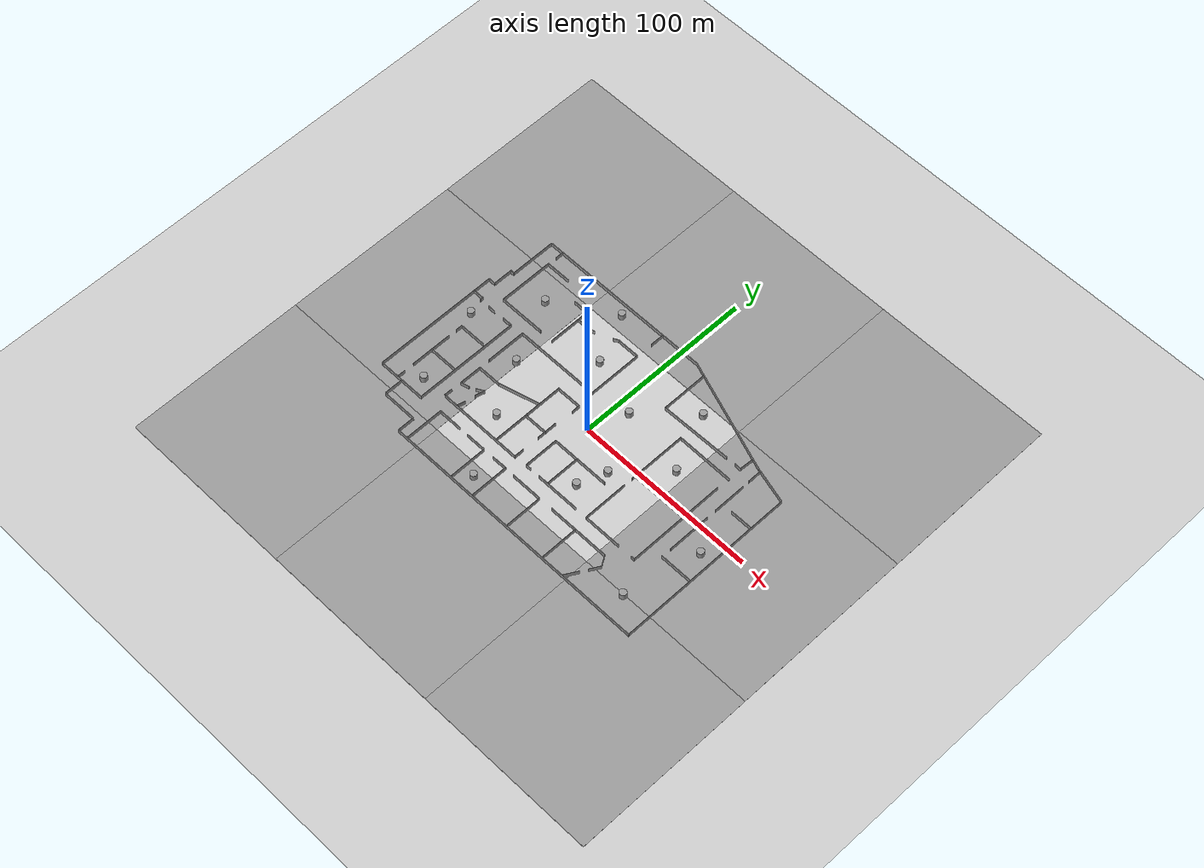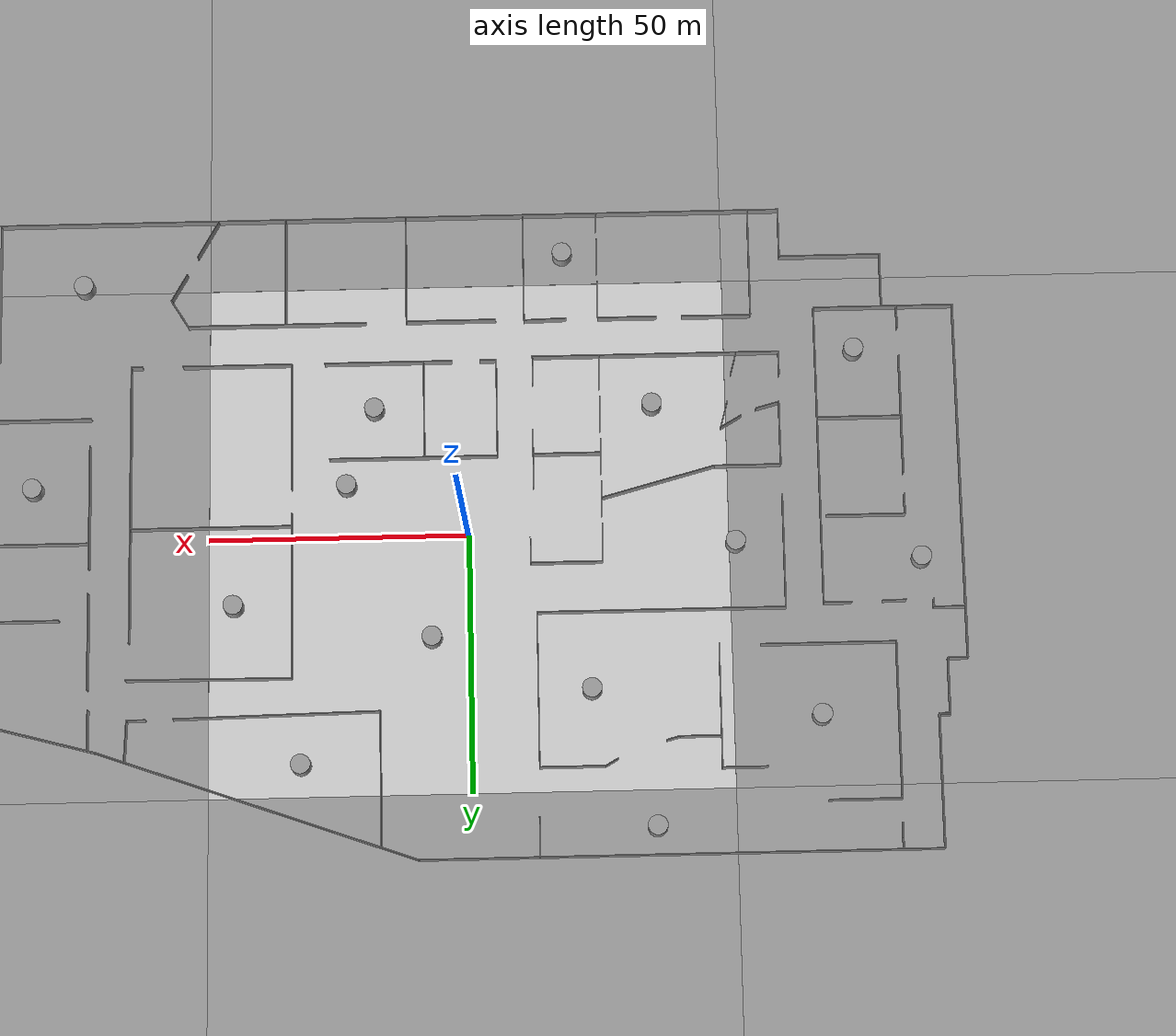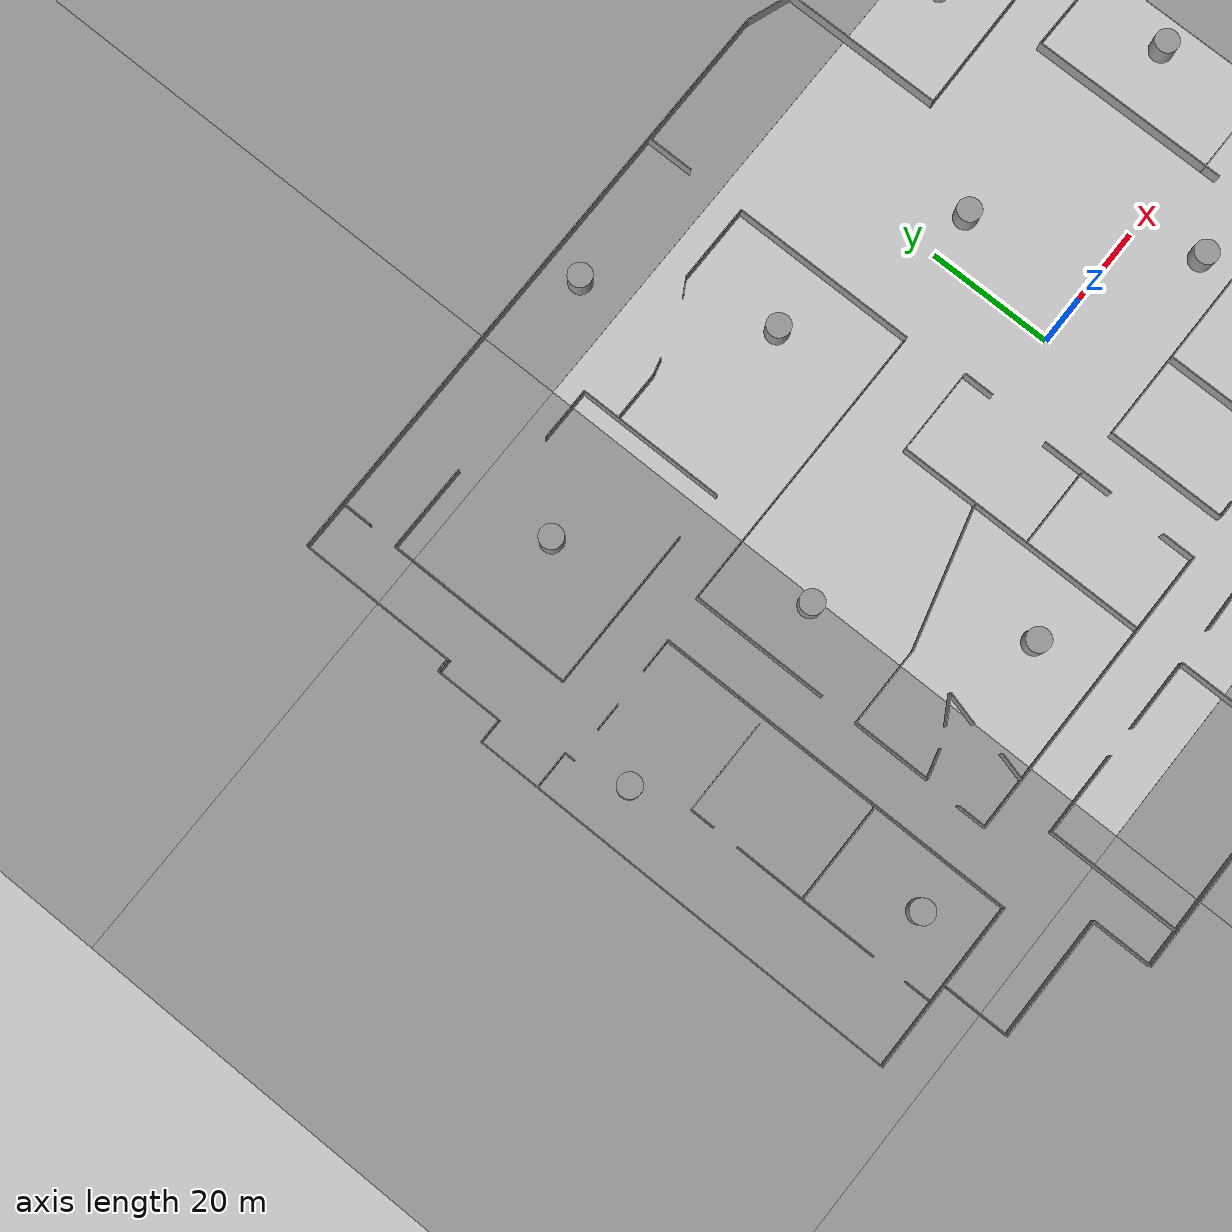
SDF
<sdf version="1.6">
 <world name="default">
  <light name="sun" type="directional">
   <pose>0 0 10 0 -0 0</pose>
   <diffuse>0.8 0.8 0.8 1</diffuse>
   <specular>0.2 0.2 0.2 1</specular>
   <attenuation>
    <range>1000</range>
    <constant>0.9</constant>
    <linear>0.01</linear>
    <quadratic>0.001</quadratic>
   </attenuation>
   <direction>-0.5 0.1 -0.9</direction>
  </light>
  <model name="ground_plane">
   <static>1</static>
   <link name="link">
    <collision name="collision">
     <geometry><plane><normal>0 0 1</normal><size>100 100</size></plane></geometry>
     <surface>
      <contact><collide_bitmask>65535</collide_bitmask></contact>
      <friction><ode><mu>100</mu><mu2>50</mu2></ode></friction>
     </surface>
    </collision>
    <visual name="visual">
     <cast_shadows>0</cast_shadows>
     <geometry><plane><normal>0 0 1</normal><size>100 100</size></plane></geometry>
     <material>
      <script><uri>file://media/materials/scripts/gazebo.material</uri><name>Gazebo/Grey</name></script>
     </material>
    </visual>
   </link>
  </model>
  <gravity>0 0 -9.8</gravity>
  <magnetic_field>6e-06 2.3e-05 -4.2e-05</magnetic_field>
  <atmosphere type="adiabatic"/>
  <physics name="default_physics" default="0" type="ode">
   <max_step_size>0.001</max_step_size>
   <real_time_factor>1</real_time_factor>
   <real_time_update_rate>1000</real_time_update_rate>
  </physics>
  <scene><ambient>0.4 0.4 0.4 1</ambient><background>0.7 0.7 0.7 1</background><shadows>1</shadows></scene>
  <spherical_coordinates>
   <surface_model>EARTH_WGS84</surface_model>
   <latitude_deg>0</latitude_deg>
   <longitude_deg>0</longitude_deg>
   <elevation>0</elevation>
   <heading_deg>0</heading_deg>
  </spherical_coordinates>
  <model name="200x200">
   <pose>-1.934 -0.6282 0 0 -0 0</pose>
   <link name="Wall_1">
    <collision name="Wall_1_Collision">
     <geometry><box><size>2 0.15 2.5</size></box></geometry>
     <pose>0 0 1.25 0 -0 0</pose>
    </collision>
    <visual name="Wall_1_Visual">
     <pose>0 0 1.25 0 -0 0</pose>
     <geometry><box><size>2 0.15 2.5</size></box></geometry>
     <material>
      <script><uri>file://media/materials/scripts/gazebo.material</uri><name>Gazebo/Grey</name></script>
      <ambient>1 1 1 1</ambient>
     </material>
     <meta><layer>0</layer></meta>
    </visual>
    <pose>-88.1339 37.765 0 0 -0 3.14159</pose>
   </link>
   <link name="Wall_10">
    <collision name="Wall_10_Collision">
     <geometry><box><size>2.16821 0.15 2.5</size></box></geometry>
     <pose>0 0 1.25 0 -0 0</pose>
    </collision>
    <visual name="Wall_10_Visual">
     <pose>0 0 1.25 0 -0 0</pose>
     <geometry><box><size>2.16821 0.15 2.5</size></box></geometry>
     <material>
      <script><uri>file://media/materials/scripts/gazebo.material</uri><name>Gazebo/Grey</name></script>
      <ambient>1 1 1 1</ambient>
     </material>
     <meta><layer>0</layer></meta>
    </visual>
    <pose>-88.0244 37.494 0 0 -0 -3.12123</pose>
   </link>
   <link name="Wall_100">
    <collision name="Wall_100_Collision">
     <geometry><box><size>21.5 0.15 2.5</size></box></geometry>
     <pose>0 0 1.25 0 -0 0</pose>
    </collision>
    <visual name="Wall_100_Visual">
     <pose>0 0 1.25 0 -0 0</pose>
     <geometry><box><size>21.5 0.15 2.5</size></box></geometry>
     <material>
      <script><uri>file://media/materials/scripts/gazebo.material</uri><name>Gazebo/Grey</name></script>
      <ambient>1 1 1 1</ambient>
     </material>
     <meta><layer>0</layer></meta>
    </visual>
    <pose>-9.33183 -52.4163 0 0 -0 -1.5708</pose>
   </link>
   <link name="Wall_102">
    <collision name="Wall_102_Collision">
     <geometry><box><size>17.5 0.15 2.5</size></box></geometry>
     <pose>0 0 1.25 0 -0 0</pose>
    </collision>
    <visual name="Wall_102_Visual">
     <pose>0 0 1.25 0 -0 0</pose>
     <geometry><box><size>17.5 0.15 2.5</size></box></geometry>
     <material>
      <script><uri>file://media/materials/scripts/gazebo.material</uri><name>Gazebo/Grey</name></script>
      <ambient>1 1 1 1</ambient>
     </material>
     <meta><layer>0</layer></meta>
    </visual>
    <pose>4.91351 -41.9689 0 0 -0 0</pose>
   </link>
   <link name="Wall_103">
    <collision name="Wall_103_Collision">
     <geometry><box><size>21.25 0.15 2.5</size></box></geometry>
     <pose>0 0 1.25 0 -0 0</pose>
    </collision>
    <visual name="Wall_103_Visual">
     <pose>0 0 1.25 0 -0 0</pose>
     <geometry><box><size>21.25 0.15 2.5</size></box></geometry>
     <material>
      <script><uri>file://media/materials/scripts/gazebo.material</uri><name>Gazebo/Grey</name></script>
      <ambient>1 1 1 1</ambient>
     </material>
     <meta><layer>0</layer></meta>
    </visual>
    <pose>13.5885 -52.5189 0 0 -0 -1.5708</pose>
   </link>
   <link name="Wall_105">
    <collision name="Wall_105_Collision">
     <geometry><box><size>34.75 0.15 2.5</size></box></geometry>
     <pose>0 0 1.25 0 -0 0</pose>
    </collision>
    <visual name="Wall_105_Visual">
     <pose>0 0 1.25 0 -0 0</pose>
     <geometry><box><size>34.75 0.15 2.5</size></box></geometry>
     <material>
      <script><uri>file://media/materials/scripts/gazebo.material</uri><name>Gazebo/Grey</name></script>
      <ambient>1 1 1 1</ambient>
     </material>
     <meta><layer>0</layer></meta>
    </visual>
    <pose>38.7694 -41.8672 0 0 -0 0</pose>
   </link>
   <link name="Wall_106">
    <collision name="Wall_106_Collision">
     <geometry><box><size>6.26653 0.15 2.5</size></box></geometry>
     <pose>0 0 1.25 0 -0 0</pose>
    </collision>
    <visual name="Wall_106_Visual">
     <pose>0 0 1.25 0 -0 0</pose>
     <geometry><box><size>6.26653 0.15 2.5</size></box></geometry>
     <material>
      <script><uri>file://media/materials/scripts/gazebo.material</uri><name>Gazebo/Grey</name></script>
      <ambient>1 1 1 1</ambient>
     </material>
     <meta><layer>0</layer></meta>
    </visual>
    <pose>57.69 -44.5564 0 0 -0 -1.0123</pose>
   </link>
   <link name="Wall_107">
    <collision name="Wall_107_Collision">
     <geometry><box><size>6.25 0.15 2.5</size></box></geometry>
     <pose>0 0 1.25 0 -0 0</pose>
    </collision>
    <visual name="Wall_107_Visual">
     <pose>0 0 1.25 0 -0 0</pose>
     <geometry><box><size>6.25 0.15 2.5</size></box></geometry>
     <material>
      <script><uri>file://media/materials/scripts/gazebo.material</uri><name>Gazebo/Grey</name></script>
      <ambient>1 1 1 1</ambient>
     </material>
     <meta><layer>0</layer></meta>
    </visual>
    <pose>57.7856 -49.7913 0 0 -0 -2.0944</pose>
   </link>
   <link name="Wall_11">
    <collision name="Wall_11_Collision">
     <geometry><box><size>10.75 0.15 2.5</size></box></geometry>
     <pose>0 0 1.25 0 -0 0</pose>
    </collision>
    <visual name="Wall_11_Visual">
     <pose>0 0 1.25 0 -0 0</pose>
     <geometry><box><size>10.75 0.15 2.5</size></box></geometry>
     <material>
      <script><uri>file://media/materials/scripts/gazebo.material</uri><name>Gazebo/Grey</name></script>
      <ambient>1 1 1 1</ambient>
     </material>
     <meta><layer>0</layer></meta>
    </visual>
    <pose>-89.0333 32.1734 0 0 -0 -1.5708</pose>
   </link>
   <link name="Wall_110">
    <collision name="Wall_110_Collision">
     <geometry><box><size>8.25 0.15 2.5</size></box></geometry>
     <pose>0 0 1.25 0 -0 0</pose>
    </collision>
    <visual name="Wall_110_Visual">
     <pose>0 0 1.25 0 -0 0</pose>
     <geometry><box><size>8.25 0.15 2.5</size></box></geometry>
     <material>
      <script><uri>file://media/materials/scripts/gazebo.material</uri><name>Gazebo/Grey</name></script>
      <ambient>1 1 1 1</ambient>
     </material>
     <meta><layer>0</layer></meta>
    </visual>
    <pose>52.2169 -59.5102 0 0 -0 -2.0944</pose>
   </link>
   <link name="Wall_112">
    <collision name="Wall_112_Collision">
     <geometry><box><size>21.25 0.15 2.5</size></box></geometry>
     <pose>0 0 1.25 0 -0 0</pose>
    </collision>
    <visual name="Wall_112_Visual">
     <pose>0 0 1.25 0 -0 0</pose>
     <geometry><box><size>21.25 0.15 2.5</size></box></geometry>
     <material>
      <script><uri>file://media/materials/scripts/gazebo.material</uri><name>Gazebo/Grey</name></script>
      <ambient>1 1 1 1</ambient>
     </material>
     <meta><layer>0</layer></meta>
    </visual>
    <pose>37.0784 -52.4679 0 0 -0 -1.5708</pose>
   </link>
   <link name="Wall_114">
    <collision name="Wall_114_Collision">
     <geometry><box><size>4.75 0.15 2.5</size></box></geometry>
     <pose>0 0 1.25 0 -0 0</pose>
    </collision>
    <visual name="Wall_114_Visual">
     <pose>0 0 1.25 0 -0 0</pose>
     <geometry><box><size>4.75 0.15 2.5</size></box></geometry>
     <material>
      <script><uri>file://media/materials/scripts/gazebo.material</uri><name>Gazebo/Grey</name></script>
      <ambient>1 1 1 1</ambient>
     </material>
     <meta><layer>0</layer></meta>
    </visual>
    <pose>-56.2329 -23.5876 0 0 -0 0.261799</pose>
   </link>
   <link name="Wall_116">
    <collision name="Wall_116_Collision">
     <geometry><box><size>4.75 0.15 2.5</size></box></geometry>
     <pose>0 0 1.25 0 -0 0</pose>
    </collision>
    <visual name="Wall_116_Visual">
     <pose>0 0 1.25 0 -0 0</pose>
     <geometry><box><size>4.75 0.15 2.5</size></box></geometry>
     <material>
      <script><uri>file://media/materials/scripts/gazebo.material</uri><name>Gazebo/Grey</name></script>
      <ambient>1 1 1 1</ambient>
     </material>
     <meta><layer>0</layer></meta>
    </visual>
    <pose>-49.033 -20.4831 0 0 -0 0.523599</pose>
   </link>
   <link name="Wall_117">
    <collision name="Wall_117_Collision">
     <geometry><box><size>5.5 0.15 2.5</size></box></geometry>
     <pose>0 0 1.25 0 -0 0</pose>
    </collision>
    <visual name="Wall_117_Visual">
     <pose>0 0 1.25 0 -0 0</pose>
     <geometry><box><size>5.5 0.15 2.5</size></box></geometry>
     <material>
      <script><uri>file://media/materials/scripts/gazebo.material</uri><name>Gazebo/Grey</name></script>
      <ambient>1 1 1 1</ambient>
     </material>
     <meta><layer>0</layer></meta>
    </visual>
    <pose>-47.7335 -21.9169 0 0 -0 -1.8326</pose>
   </link>
   <link name="Wall_119">
    <collision name="Wall_119_Collision">
     <geometry><box><size>4.5 0.15 2.5</size></box></geometry>
     <pose>0 0 1.25 0 -0 0</pose>
    </collision>
    <visual name="Wall_119_Visual">
     <pose>0 0 1.25 0 -0 0</pose>
     <geometry><box><size>4.5 0.15 2.5</size></box></geometry>
     <material>
      <script><uri>file://media/materials/scripts/gazebo.material</uri><name>Gazebo/Grey</name></script>
      <ambient>1 1 1 1</ambient>
     </material>
     <meta><layer>0</layer></meta>
    </visual>
    <pose>-49.8293 -32.1308 0 0 -0 -1.8326</pose>
   </link>
   <link name="Wall_12">
    <collision name="Wall_12_Collision">
     <geometry><box><size>4 0.15 2.5</size></box></geometry>
     <pose>0 0 1.25 0 -0 0</pose>
    </collision>
    <visual name="Wall_12_Visual">
     <pose>0 0 1.25 0 -0 0</pose>
     <geometry><box><size>4 0.15 2.5</size></box></geometry>
     <material>
      <script><uri>file://media/materials/scripts/gazebo.material</uri><name>Gazebo/Grey</name></script>
      <ambient>1 1 1 1</ambient>
     </material>
     <meta><layer>0</layer></meta>
    </visual>
    <pose>-90.9583 26.8734 0 0 -0 3.14159</pose>
   </link>
   <link name="Wall_121">
    <collision name="Wall_121_Collision">
     <geometry><box><size>15.25 0.15 2.5</size></box></geometry>
     <pose>0 0 1.25 0 -0 0</pose>
    </collision>
    <visual name="Wall_121_Visual">
     <pose>0 0 1.25 0 -0 0</pose>
     <geometry><box><size>15.25 0.15 2.5</size></box></geometry>
     <material>
      <script><uri>file://media/materials/scripts/gazebo.material</uri><name>Gazebo/Grey</name></script>
      <ambient>1 1 1 1</ambient>
     </material>
     <meta><layer>0</layer></meta>
    </visual>
    <pose>-74.4745 -1.46643 0 0 -0 3.14159</pose>
   </link>
   <link name="Wall_122">
    <collision name="Wall_122_Collision">
     <geometry><box><size>4 0.15 2.5</size></box></geometry>
     <pose>0 0 1.25 0 -0 0</pose>
    </collision>
    <visual name="Wall_122_Visual">
     <pose>0 0 1.25 0 -0 0</pose>
     <geometry><box><size>4 0.15 2.5</size></box></geometry>
     <material>
      <script><uri>file://media/materials/scripts/gazebo.material</uri><name>Gazebo/Grey</name></script>
      <ambient>1 1 1 1</ambient>
     </material>
     <meta><layer>0</layer></meta>
    </visual>
    <pose>-82.0245 -3.39143 0 0 -0 -1.5708</pose>
   </link>
   <link name="Wall_124">
    <collision name="Wall_124_Collision">
     <geometry><box><size>23.5 0.15 2.5</size></box></geometry>
     <pose>0 0 1.25 0 -0 0</pose>
    </collision>
    <visual name="Wall_124_Visual">
     <pose>0 0 1.25 0 -0 0</pose>
     <geometry><box><size>23.5 0.15 2.5</size></box></geometry>
     <material>
      <script><uri>file://media/materials/scripts/gazebo.material</uri><name>Gazebo/Grey</name></script>
      <ambient>1 1 1 1</ambient>
     </material>
     <meta><layer>0</layer></meta>
    </visual>
    <pose>-82.0598 -21.3227 0 0 -0 -1.5708</pose>
   </link>
   <link name="Wall_126">
    <collision name="Wall_126_Collision">
     <geometry><box><size>16.25 0.15 2.5</size></box></geometry>
     <pose>0 0 1.25 0 -0 0</pose>
    </collision>
    <visual name="Wall_126_Visual">
     <pose>0 0 1.25 0 -0 0</pose>
     <geometry><box><size>16.25 0.15 2.5</size></box></geometry>
     <material>
      <script><uri>file://media/materials/scripts/gazebo.material</uri><name>Gazebo/Grey</name></script>
      <ambient>1 1 1 1</ambient>
     </material>
     <meta><layer>0</layer></meta>
    </visual>
    <pose>-73.9643 -20.8969 0 0 -0 0</pose>
   </link>
   <link name="Wall_128">
    <collision name="Wall_128_Collision">
     <geometry><box><size>4.5 0.15 2.5</size></box></geometry>
     <pose>0 0 1.25 0 -0 0</pose>
    </collision>
    <visual name="Wall_128_Visual">
     <pose>0 0 1.25 0 -0 0</pose>
     <geometry><box><size>4.5 0.15 2.5</size></box></geometry>
     <material>
      <script><uri>file://media/materials/scripts/gazebo.material</uri><name>Gazebo/Grey</name></script>
      <ambient>1 1 1 1</ambient>
     </material>
     <meta><layer>0</layer></meta>
    </visual>
    <pose>-81.9745 -40.7846 0 0 -0 -1.5708</pose>
   </link>
   <link name="Wall_13">
    <collision name="Wall_13_Collision">
     <geometry><box><size>70 0.15 2.5</size></box></geometry>
     <pose>0 0 1.25 0 -0 0</pose>
    </collision>
    <visual name="Wall_13_Visual">
     <pose>0 0 1.25 0 -0 0</pose>
     <geometry><box><size>70 0.15 2.5</size></box></geometry>
     <material>
      <script><uri>file://media/materials/scripts/gazebo.material</uri><name>Gazebo/Grey</name></script>
      <ambient>1 1 1 1</ambient>
     </material>
     <meta><layer>0</layer></meta>
    </visual>
    <pose>-92.8833 -8.05159 0 0 -0 -1.5708</pose>
   </link>
   <link name="Wall_132">
    <collision name="Wall_132_Collision">
     <geometry><box><size>26 0.15 2.5</size></box></geometry>
     <pose>0 0 1.25 0 -0 0</pose>
    </collision>
    <visual name="Wall_132_Visual">
     <pose>0 0 1.25 0 -0 0</pose>
     <geometry><box><size>26 0.15 2.5</size></box></geometry>
     <material>
      <script><uri>file://media/materials/scripts/gazebo.material</uri><name>Gazebo/Grey</name></script>
      <ambient>1 1 1 1</ambient>
     </material>
     <meta><layer>0</layer></meta>
    </visual>
    <pose>19.1403 47.6641 0 0 -0 -1.5708</pose>
   </link>
   <link name="Wall_133">
    <collision name="Wall_133_Collision">
     <geometry><box><size>39.4868 0.15 2.5</size></box></geometry>
     <pose>0 0 1.25 0 -0 0</pose>
    </collision>
    <visual name="Wall_133_Visual">
     <pose>0 0 1.25 0 -0 0</pose>
     <geometry><box><size>39.4868 0.15 2.5</size></box></geometry>
     <material>
      <script><uri>file://media/materials/scripts/gazebo.material</uri><name>Gazebo/Grey</name></script>
      <ambient>1 1 1 1</ambient>
     </material>
     <meta><layer>0</layer></meta>
    </visual>
    <pose>38.8057 35.0158 0 0 -0 0.017285</pose>
   </link>
   <link name="Wall_135">
    <collision name="Wall_135_Collision">
     <geometry><box><size>3.75488 0.15 2.5</size></box></geometry>
     <pose>0 0 1.25 0 -0 0</pose>
    </collision>
    <visual name="Wall_135_Visual">
     <pose>0 0 1.25 0 -0 0</pose>
     <geometry><box><size>3.75488 0.15 2.5</size></box></geometry>
     <material>
      <script><uri>file://media/materials/scripts/gazebo.material</uri><name>Gazebo/Grey</name></script>
      <ambient>1 1 1 1</ambient>
     </material>
     <meta><layer>0</layer></meta>
    </visual>
    <pose>65.5332 35.4234 0 0 -0 0</pose>
   </link>
   <link name="Wall_136">
    <collision name="Wall_136_Collision">
     <geometry><box><size>7.97058 0.15 2.5</size></box></geometry>
     <pose>0 0 1.25 0 -0 0</pose>
    </collision>
    <visual name="Wall_136_Visual">
     <pose>0 0 1.25 0 -0 0</pose>
     <geometry><box><size>7.97058 0.15 2.5</size></box></geometry>
     <material>
      <script><uri>file://media/materials/scripts/gazebo.material</uri><name>Gazebo/Grey</name></script>
      <ambient>1 1 1 1</ambient>
     </material>
     <meta><layer>0</layer></meta>
    </visual>
    <pose>67.5318 39.3778 0 0 -0 1.52063</pose>
   </link>
   <link name="Wall_138">
    <collision name="Wall_138_Collision">
     <geometry><box><size>7.75 0.15 2.5</size></box></geometry>
     <pose>0 0 1.25 0 -0 0</pose>
    </collision>
    <visual name="Wall_138_Visual">
     <pose>0 0 1.25 0 -0 0</pose>
     <geometry><box><size>7.75 0.15 2.5</size></box></geometry>
     <material>
      <script><uri>file://media/materials/scripts/gazebo.material</uri><name>Gazebo/Grey</name></script>
      <ambient>1 1 1 1</ambient>
     </material>
     <meta><layer>0</layer></meta>
    </visual>
    <pose>74.7284 37.1199 0 0 -0 -1.5708</pose>
   </link>
   <link name="Wall_14">
    <collision name="Wall_14_Collision">
     <geometry><box><size>27.25 0.15 2.5</size></box></geometry>
     <pose>0 0 1.25 0 -0 0</pose>
    </collision>
    <visual name="Wall_14_Visual">
     <pose>0 0 1.25 0 -0 0</pose>
     <geometry><box><size>27.25 0.15 2.5</size></box></geometry>
     <material>
      <script><uri>file://media/materials/scripts/gazebo.material</uri><name>Gazebo/Grey</name></script>
      <ambient>1 1 1 1</ambient>
     </material>
     <meta><layer>0</layer></meta>
    </visual>
    <pose>-79.3333 -42.9766 0 0 -0 0</pose>
   </link>
   <link name="Wall_140">
    <collision name="Wall_140_Collision">
     <geometry><box><size>18.75 0.15 2.5</size></box></geometry>
     <pose>0 0 1.25 0 -0 0</pose>
    </collision>
    <visual name="Wall_140_Visual">
     <pose>0 0 1.25 0 -0 0</pose>
     <geometry><box><size>18.75 0.15 2.5</size></box></geometry>
     <material>
      <script><uri>file://media/materials/scripts/gazebo.material</uri><name>Gazebo/Grey</name></script>
      <ambient>1 1 1 1</ambient>
     </material>
     <meta><layer>0</layer></meta>
    </visual>
    <pose>74.8898 20.0424 0 0 -0 -1.5708</pose>
   </link>
   <link name="Wall_142">
    <collision name="Wall_142_Collision">
     <geometry><box><size>24.25 0.15 2.5</size></box></geometry>
     <pose>0 0 1.25 0 -0 0</pose>
    </collision>
    <visual name="Wall_142_Visual">
     <pose>0 0 1.25 0 -0 0</pose>
     <geometry><box><size>24.25 0.15 2.5</size></box></geometry>
     <material>
      <script><uri>file://media/materials/scripts/gazebo.material</uri><name>Gazebo/Grey</name></script>
      <ambient>1 1 1 1</ambient>
     </material>
     <meta><layer>0</layer></meta>
    </visual>
    <pose>74.8898 -6.2518 0 0 -0 -1.5708</pose>
   </link>
   <link name="Wall_144">
    <collision name="Wall_144_Collision">
     <geometry><box><size>18.25 0.15 2.5</size></box></geometry>
     <pose>0 0 1.25 0 -0 0</pose>
    </collision>
    <visual name="Wall_144_Visual">
     <pose>0 0 1.25 0 -0 0</pose>
     <geometry><box><size>18.25 0.15 2.5</size></box></geometry>
     <material>
      <script><uri>file://media/materials/scripts/gazebo.material</uri><name>Gazebo/Grey</name></script>
      <ambient>1 1 1 1</ambient>
     </material>
     <meta><layer>0</layer></meta>
    </visual>
    <pose>83.7898 -23.7446 0 0 -0 0</pose>
   </link>
   <link name="Wall_146">
    <collision name="Wall_146_Collision">
     <geometry><box><size>12.5 0.15 2.5</size></box></geometry>
     <pose>0 0 1.25 0 -0 0</pose>
    </collision>
    <visual name="Wall_146_Visual">
     <pose>0 0 1.25 0 -0 0</pose>
     <geometry><box><size>12.5 0.15 2.5</size></box></geometry>
     <material>
      <script><uri>file://media/materials/scripts/gazebo.material</uri><name>Gazebo/Grey</name></script>
      <ambient>1 1 1 1</ambient>
     </material>
     <meta><layer>0</layer></meta>
    </visual>
    <pose>86.6134 15.8457 0 0 -0 0</pose>
   </link>
   <link name="Wall_149">
    <collision name="Wall_149_Collision">
     <geometry><box><size>18 0.15 2.5</size></box></geometry>
     <pose>0 0 1.25 0 -0 0</pose>
    </collision>
    <visual name="Wall_149_Visual">
     <pose>0 0 1.25 0 -0 0</pose>
     <geometry><box><size>18 0.15 2.5</size></box></geometry>
     <material>
      <script><uri>file://media/materials/scripts/gazebo.material</uri><name>Gazebo/Grey</name></script>
      <ambient>1 1 1 1</ambient>
     </material>
     <meta><layer>0</layer></meta>
    </visual>
    <pose>83.8483 0.888992 0 0 -0 0</pose>
   </link>
   <link name="Wall_15">
    <collision name="Wall_15_Collision">
     <geometry><box><size>58.75 0.15 2.5</size></box></geometry>
     <pose>0 0 1.25 0 -0 0</pose>
    </collision>
    <visual name="Wall_15_Visual">
     <pose>0 0 1.25 0 -0 0</pose>
     <geometry><box><size>58.75 0.15 2.5</size></box></geometry>
     <material>
      <script><uri>file://media/materials/scripts/gazebo.material</uri><name>Gazebo/Grey</name></script>
      <ambient>1 1 1 1</ambient>
     </material>
     <meta><layer>0</layer></meta>
    </visual>
    <pose>-65.7833 -13.6766 0 0 -0 1.5708</pose>
   </link>
   <link name="Wall_151">
    <collision name="Wall_151_Collision">
     <geometry><box><size>7.75 0.15 2.5</size></box></geometry>
     <pose>0 0 1.25 0 -0 0</pose>
    </collision>
    <visual name="Wall_151_Visual">
     <pose>0 0 1.25 0 -0 0</pose>
     <geometry><box><size>7.75 0.15 2.5</size></box></geometry>
     <material>
      <script><uri>file://media/materials/scripts/gazebo.material</uri><name>Gazebo/Grey</name></script>
      <ambient>1 1 1 1</ambient>
     </material>
     <meta><layer>0</layer></meta>
    </visual>
    <pose>-10.7428 59.3502 0 0 -0 -1.5708</pose>
   </link>
   <link name="Wall_153">
    <collision name="Wall_153_Collision">
     <geometry><box><size>1.75 0.15 2.5</size></box></geometry>
     <pose>0 0 1.25 0 -0 0</pose>
    </collision>
    <visual name="Wall_153_Visual">
     <pose>0 0 1.25 0 -0 0</pose>
     <geometry><box><size>1.75 0.15 2.5</size></box></geometry>
     <material>
      <script><uri>file://media/materials/scripts/gazebo.material</uri><name>Gazebo/Grey</name></script>
      <ambient>1 1 1 1</ambient>
     </material>
     <meta><layer>0</layer></meta>
    </visual>
    <pose>-86.8358 16.1079 0 0 -0 -1.5708</pose>
   </link>
   <link name="Wall_16">
    <collision name="Wall_16_Collision">
     <geometry><box><size>5.5 0.15 2.5</size></box></geometry>
     <pose>0 0 1.25 0 -0 0</pose>
    </collision>
    <visual name="Wall_16_Visual">
     <pose>0 0 1.25 0 -0 0</pose>
     <geometry><box><size>5.5 0.15 2.5</size></box></geometry>
     <material>
      <script><uri>file://media/materials/scripts/gazebo.material</uri><name>Gazebo/Grey</name></script>
      <ambient>1 1 1 1</ambient>
     </material>
     <meta><layer>0</layer></meta>
    </visual>
    <pose>-68.4583 15.6234 0 0 -0 3.14159</pose>
   </link>
   <link name="Wall_18">
    <collision name="Wall_18_Collision">
     <geometry><box><size>4.5 0.15 2.5</size></box></geometry>
     <pose>0 0 1.25 0 -0 0</pose>
    </collision>
    <visual name="Wall_18_Visual">
     <pose>0 0 1.25 0 -0 0</pose>
     <geometry><box><size>4.5 0.15 2.5</size></box></geometry>
     <material>
      <script><uri>file://media/materials/scripts/gazebo.material</uri><name>Gazebo/Grey</name></script>
      <ambient>1 1 1 1</ambient>
     </material>
     <meta><layer>0</layer></meta>
    </visual>
    <pose>-79.2848 15.4422 0 0 -0 0</pose>
   </link>
   <link name="Wall_20">
    <collision name="Wall_20_Collision">
     <geometry><box><size>6.14833 0.15 2.5</size></box></geometry>
     <pose>0 0 1.25 0 -0 0</pose>
    </collision>
    <visual name="Wall_20_Visual">
     <pose>0 0 1.25 0 -0 0</pose>
     <geometry><box><size>6.14833 0.15 2.5</size></box></geometry>
     <material>
      <script><uri>file://media/materials/scripts/gazebo.material</uri><name>Gazebo/Grey</name></script>
      <ambient>1 1 1 1</ambient>
     </material>
     <meta><layer>0</layer></meta>
    </visual>
    <pose>-89.835 16.9079 0 0 -0 0</pose>
   </link>
   <link name="Wall_23">
    <collision name="Wall_23_Collision">
     <geometry><box><size>10.25 0.15 2.5</size></box></geometry>
     <pose>0 0 1.25 0 -0 0</pose>
    </collision>
    <visual name="Wall_23_Visual">
     <pose>0 0 1.25 0 -0 0</pose>
     <geometry><box><size>10.25 0.15 2.5</size></box></geometry>
     <material>
      <script><uri>file://media/materials/scripts/gazebo.material</uri><name>Gazebo/Grey</name></script>
      <ambient>1 1 1 1</ambient>
     </material>
     <meta><layer>0</layer></meta>
    </visual>
    <pose>-79.0836 -48.5195 0 0 -0 -1.5708</pose>
   </link>
   <link name="Wall_24">
    <collision name="Wall_24_Collision">
     <geometry><box><size>19.75 0.15 2.5</size></box></geometry>
     <pose>0 0 1.25 0 -0 0</pose>
    </collision>
    <visual name="Wall_24_Visual">
     <pose>0 0 1.25 0 -0 0</pose>
     <geometry><box><size>19.75 0.15 2.5</size></box></geometry>
     <material>
      <script><uri>file://media/materials/scripts/gazebo.material</uri><name>Gazebo/Grey</name></script>
      <ambient>1 1 1 1</ambient>
     </material>
     <meta><layer>0</layer></meta>
    </visual>
    <pose>-69.2836 -53.5695 0 0 -0 0</pose>
   </link>
   <link name="Wall_25">
    <collision name="Wall_25_Collision">
     <geometry><box><size>9.75 0.15 2.5</size></box></geometry>
     <pose>0 0 1.25 0 -0 0</pose>
    </collision>
    <visual name="Wall_25_Visual">
     <pose>0 0 1.25 0 -0 0</pose>
     <geometry><box><size>9.75 0.15 2.5</size></box></geometry>
     <material>
      <script><uri>file://media/materials/scripts/gazebo.material</uri><name>Gazebo/Grey</name></script>
      <ambient>1 1 1 1</ambient>
     </material>
     <meta><layer>0</layer></meta>
    </visual>
    <pose>-59.4836 -58.3695 0 0 -0 -1.5708</pose>
   </link>
   <link name="Wall_26">
    <collision name="Wall_26_Collision">
     <geometry><box><size>152.501 0.15 2.5</size></box></geometry>
     <pose>0 0 1.25 0 -0 0</pose>
    </collision>
    <visual name="Wall_26_Visual">
     <pose>0 0 1.25 0 -0 0</pose>
     <geometry><box><size>152.501 0.15 2.5</size></box></geometry>
     <material>
      <script><uri>file://media/materials/scripts/gazebo.material</uri><name>Gazebo/Grey</name></script>
      <ambient>1 1 1 1</ambient>
     </material>
     <meta><layer>0</layer></meta>
    </visual>
    <pose>16.6914 -63.1695 0 0 -0 0</pose>
   </link>
   <link name="Wall_27">
    <collision name="Wall_27_Collision">
     <geometry><box><size>99.5 0.15 2.5</size></box></geometry>
     <pose>0 0 1.25 0 -0 0</pose>
    </collision>
    <visual name="Wall_27_Visual">
     <pose>0 0 1.25 0 -0 0</pose>
     <geometry><box><size>99.5 0.15 2.5</size></box></geometry>
     <material>
      <script><uri>file://media/materials/scripts/gazebo.material</uri><name>Gazebo/Grey</name></script>
      <ambient>1 1 1 1</ambient>
     </material>
     <meta><layer>0</layer></meta>
    </visual>
    <pose>92.8664 -13.4945 0 0 -0 1.5708</pose>
   </link>
   <link name="Wall_28">
    <collision name="Wall_28_Collision">
     <geometry><box><size>20.5 0.15 2.5</size></box></geometry>
     <pose>0 0 1.25 0 -0 0</pose>
    </collision>
    <visual name="Wall_28_Visual">
     <pose>0 0 1.25 0 -0 0</pose>
     <geometry><box><size>20.5 0.15 2.5</size></box></geometry>
     <material>
      <script><uri>file://media/materials/scripts/gazebo.material</uri><name>Gazebo/Grey</name></script>
      <ambient>1 1 1 1</ambient>
     </material>
     <meta><layer>0</layer></meta>
    </visual>
    <pose>83.0381 38.814 0 0 -0 2.87979</pose>
   </link>
   <link name="Wall_29">
    <collision name="Wall_29_Collision">
     <geometry><box><size>65.0274 0.15 2.5</size></box></geometry>
     <pose>0 0 1.25 0 -0 0</pose>
    </collision>
    <visual name="Wall_29_Visual">
     <pose>0 0 1.25 0 -0 0</pose>
     <geometry><box><size>65.0274 0.15 2.5</size></box></geometry>
     <material>
      <script><uri>file://media/materials/scripts/gazebo.material</uri><name>Gazebo/Grey</name></script>
      <ambient>1 1 1 1</ambient>
     </material>
     <meta><layer>0</layer></meta>
    </visual>
    <pose>42.6397 52.2981 0 0 -0 2.80052</pose>
   </link>
   <link name="Wall_30">
    <collision name="Wall_30_Collision">
     <geometry><box><size>99.25 0.15 2.5</size></box></geometry>
     <pose>0 0 1.25 0 -0 0</pose>
    </collision>
    <visual name="Wall_30_Visual">
     <pose>0 0 1.25 0 -0 0</pose>
     <geometry><box><size>99.25 0.15 2.5</size></box></geometry>
     <material>
      <script><uri>file://media/materials/scripts/gazebo.material</uri><name>Gazebo/Grey</name></script>
      <ambient>1 1 1 1</ambient>
     </material>
     <meta><layer>0</layer></meta>
    </visual>
    <pose>-37.4393 63.1487 0 0 -0 3.14159</pose>
   </link>
   <link name="Wall_32">
    <collision name="Wall_32_Collision">
     <geometry><box><size>5 0.15 2.5</size></box></geometry>
     <pose>0 0 1.25 0 -0 0</pose>
    </collision>
    <visual name="Wall_32_Visual">
     <pose>0 0 1.25 0 -0 0</pose>
     <geometry><box><size>5 0.15 2.5</size></box></geometry>
     <material>
      <script><uri>file://media/materials/scripts/gazebo.material</uri><name>Gazebo/Grey</name></script>
      <ambient>1 1 1 1</ambient>
     </material>
     <meta><layer>0</layer></meta>
    </visual>
    <pose>-79.1639 60.656 0 0 -0 -1.5708</pose>
   </link>
   <link name="Wall_34">
    <collision name="Wall_34_Collision">
     <geometry><box><size>14 0.15 2.5</size></box></geometry>
     <pose>0 0 1.25 0 -0 0</pose>
    </collision>
    <visual name="Wall_34_Visual">
     <pose>0 0 1.25 0 -0 0</pose>
     <geometry><box><size>14 0.15 2.5</size></box></geometry>
     <material>
      <script><uri>file://media/materials/scripts/gazebo.material</uri><name>Gazebo/Grey</name></script>
      <ambient>1 1 1 1</ambient>
     </material>
     <meta><layer>0</layer></meta>
    </visual>
    <pose>-72.4034 53.5186 0 0 -0 3.14159</pose>
   </link>
   <link name="Wall_35">
    <collision name="Wall_35_Collision">
     <geometry><box><size>30.25 0.15 2.5</size></box></geometry>
     <pose>0 0 1.25 0 -0 0</pose>
    </collision>
    <visual name="Wall_35_Visual">
     <pose>0 0 1.25 0 -0 0</pose>
     <geometry><box><size>30.25 0.15 2.5</size></box></geometry>
     <material>
      <script><uri>file://media/materials/scripts/gazebo.material</uri><name>Gazebo/Grey</name></script>
      <ambient>1 1 1 1</ambient>
     </material>
     <meta><layer>0</layer></meta>
    </visual>
    <pose>-79.3284 38.4686 0 0 -0 -1.5708</pose>
   </link>
   <link name="Wall_36">
    <collision name="Wall_36_Collision">
     <geometry><box><size>26 0.15 2.5</size></box></geometry>
     <pose>0 0 1.25 0 -0 0</pose>
    </collision>
    <visual name="Wall_36_Visual">
     <pose>0 0 1.25 0 -0 0</pose>
     <geometry><box><size>26 0.15 2.5</size></box></geometry>
     <material>
      <script><uri>file://media/materials/scripts/gazebo.material</uri><name>Gazebo/Grey</name></script>
      <ambient>1 1 1 1</ambient>
     </material>
     <meta><layer>0</layer></meta>
    </visual>
    <pose>-66.4034 23.4186 0 0 -0 0</pose>
   </link>
   <link name="Wall_38">
    <collision name="Wall_38_Collision">
     <geometry><box><size>8.75 0.15 2.5</size></box></geometry>
     <pose>0 0 1.25 0 -0 0</pose>
    </collision>
    <visual name="Wall_38_Visual">
     <pose>0 0 1.25 0 -0 0</pose>
     <geometry><box><size>8.75 0.15 2.5</size></box></geometry>
     <material>
      <script><uri>file://media/materials/scripts/gazebo.material</uri><name>Gazebo/Grey</name></script>
      <ambient>1 1 1 1</ambient>
     </material>
     <meta><layer>0</layer></meta>
    </visual>
    <pose>-49.8525 46.9117 0 0 -0 0</pose>
   </link>
   <link name="Wall_39">
    <collision name="Wall_39_Collision">
     <geometry><box><size>24 0.15 2.5</size></box></geometry>
     <pose>0 0 1.25 0 -0 0</pose>
    </collision>
    <visual name="Wall_39_Visual">
     <pose>0 0 1.25 0 -0 0</pose>
     <geometry><box><size>24 0.15 2.5</size></box></geometry>
     <material>
      <script><uri>file://media/materials/scripts/gazebo.material</uri><name>Gazebo/Grey</name></script>
      <ambient>1 1 1 1</ambient>
     </material>
     <meta><layer>0</layer></meta>
    </visual>
    <pose>-45.5525 34.9867 0 0 -0 -1.5708</pose>
   </link>
   <link name="Wall_41">
    <collision name="Wall_41_Collision">
     <geometry><box><size>8 0.15 2.5</size></box></geometry>
     <pose>0 0 1.25 0 -0 0</pose>
    </collision>
    <visual name="Wall_41_Visual">
     <pose>0 0 1.25 0 -0 0</pose>
     <geometry><box><size>8 0.15 2.5</size></box></geometry>
     <material>
      <script><uri>file://media/materials/scripts/gazebo.material</uri><name>Gazebo/Grey</name></script>
      <ambient>1 1 1 1</ambient>
     </material>
     <meta><layer>0</layer></meta>
    </visual>
    <pose>-41.5628 40.7932 0 0 -0 0</pose>
   </link>
   <link name="Wall_42">
    <collision name="Wall_42_Collision">
     <geometry><box><size>2.75 0.15 2.5</size></box></geometry>
     <pose>0 0 1.25 0 -0 0</pose>
    </collision>
    <visual name="Wall_42_Visual">
     <pose>0 0 1.25 0 -0 0</pose>
     <geometry><box><size>2.75 0.15 2.5</size></box></geometry>
     <material>
      <script><uri>file://media/materials/scripts/gazebo.material</uri><name>Gazebo/Grey</name></script>
      <ambient>1 1 1 1</ambient>
     </material>
     <meta><layer>0</layer></meta>
    </visual>
    <pose>-36.3821 41.1296 0 0 -0 0.261799</pose>
   </link>
   <link name="Wall_44">
    <collision name="Wall_44_Collision">
     <geometry><box><size>2.75 0.15 2.5</size></box></geometry>
     <pose>0 0 1.25 0 -0 0</pose>
    </collision>
    <visual name="Wall_44_Visual">
     <pose>0 0 1.25 0 -0 0</pose>
     <geometry><box><size>2.75 0.15 2.5</size></box></geometry>
     <material>
      <script><uri>file://media/materials/scripts/gazebo.material</uri><name>Gazebo/Grey</name></script>
      <ambient>1 1 1 1</ambient>
     </material>
     <meta><layer>0</layer></meta>
    </visual>
    <pose>-24.6498 45.4668 0 0 -0 0.523599</pose>
   </link>
   <link name="Wall_45">
    <collision name="Wall_45_Collision">
     <geometry><box><size>12.75 0.15 2.5</size></box></geometry>
     <pose>0 0 1.25 0 -0 0</pose>
    </collision>
    <visual name="Wall_45_Visual">
     <pose>0 0 1.25 0 -0 0</pose>
     <geometry><box><size>12.75 0.15 2.5</size></box></geometry>
     <material>
      <script><uri>file://media/materials/scripts/gazebo.material</uri><name>Gazebo/Grey</name></script>
      <ambient>1 1 1 1</ambient>
     </material>
     <meta><layer>0</layer></meta>
    </visual>
    <pose>-17.224 46.1168 0 0 -0 0</pose>
   </link>
   <link name="Wall_46">
    <collision name="Wall_46_Collision">
     <geometry><box><size>30 0.15 2.5</size></box></geometry>
     <pose>0 0 1.25 0 -0 0</pose>
    </collision>
    <visual name="Wall_46_Visual">
     <pose>0 0 1.25 0 -0 0</pose>
     <geometry><box><size>30 0.15 2.5</size></box></geometry>
     <material>
      <script><uri>file://media/materials/scripts/gazebo.material</uri><name>Gazebo/Grey</name></script>
      <ambient>1 1 1 1</ambient>
     </material>
     <meta><layer>0</layer></meta>
    </visual>
    <pose>-10.924 31.1918 0 0 -0 -1.5708</pose>
   </link>
   <link name="Wall_47">
    <collision name="Wall_47_Collision">
     <geometry><box><size>47.75 0.15 2.5</size></box></geometry>
     <pose>0 0 1.25 0 -0 0</pose>
    </collision>
    <visual name="Wall_47_Visual">
     <pose>0 0 1.25 0 -0 0</pose>
     <geometry><box><size>47.75 0.15 2.5</size></box></geometry>
     <material>
      <script><uri>file://media/materials/scripts/gazebo.material</uri><name>Gazebo/Grey</name></script>
      <ambient>1 1 1 1</ambient>
     </material>
     <meta><layer>0</layer></meta>
    </visual>
    <pose>-34.724 16.2668 0 0 -0 3.14159</pose>
   </link>
   <link name="Wall_48">
    <collision name="Wall_48_Collision">
     <geometry><box><size>22.25 0.15 2.5</size></box></geometry>
     <pose>0 0 1.25 0 -0 0</pose>
    </collision>
    <visual name="Wall_48_Visual">
     <pose>0 0 1.25 0 -0 0</pose>
     <geometry><box><size>22.25 0.15 2.5</size></box></geometry>
     <material>
      <script><uri>file://media/materials/scripts/gazebo.material</uri><name>Gazebo/Grey</name></script>
      <ambient>1 1 1 1</ambient>
     </material>
     <meta><layer>0</layer></meta>
    </visual>
    <pose>-58.524 5.21677 0 0 -0 -1.5708</pose>
   </link>
   <link name="Wall_51">
    <collision name="Wall_51_Collision">
     <geometry><box><size>12.5 0.15 2.5</size></box></geometry>
     <pose>0 0 1.25 0 -0 0</pose>
    </collision>
    <visual name="Wall_51_Visual">
     <pose>0 0 1.25 0 -0 0</pose>
     <geometry><box><size>12.5 0.15 2.5</size></box></geometry>
     <material>
      <script><uri>file://media/materials/scripts/gazebo.material</uri><name>Gazebo/Grey</name></script>
      <ambient>1 1 1 1</ambient>
     </material>
     <meta><layer>0</layer></meta>
    </visual>
    <pose>-58.457 -17.9239 0 0 -0 1.5708</pose>
   </link>
   <link name="Wall_52">
    <collision name="Wall_52_Collision">
     <geometry><box><size>13 0.15 2.5</size></box></geometry>
     <pose>0 0 1.25 0 -0 0</pose>
    </collision>
    <visual name="Wall_52_Visual">
     <pose>0 0 1.25 0 -0 0</pose>
     <geometry><box><size>13 0.15 2.5</size></box></geometry>
     <material>
      <script><uri>file://media/materials/scripts/gazebo.material</uri><name>Gazebo/Grey</name></script>
      <ambient>1 1 1 1</ambient>
     </material>
     <meta><layer>0</layer></meta>
    </visual>
    <pose>-52.032 -11.7489 0 0 -0 0</pose>
   </link>
   <link name="Wall_53">
    <collision name="Wall_53_Collision">
     <geometry><box><size>22.75 0.15 2.5</size></box></geometry>
     <pose>0 0 1.25 0 -0 0</pose>
    </collision>
    <visual name="Wall_53_Visual">
     <pose>0 0 1.25 0 -0 0</pose>
     <geometry><box><size>22.75 0.15 2.5</size></box></geometry>
     <material>
      <script><uri>file://media/materials/scripts/gazebo.material</uri><name>Gazebo/Grey</name></script>
      <ambient>1 1 1 1</ambient>
     </material>
     <meta><layer>0</layer></meta>
    </visual>
    <pose>-34.692 -8.82426 0 0 -0 0.261799</pose>
   </link>
   <link name="Wall_57">
    <collision name="Wall_57_Collision">
     <geometry><box><size>5 0.15 2.5</size></box></geometry>
     <pose>0 0 1.25 0 -0 0</pose>
    </collision>
    <visual name="Wall_57_Visual">
     <pose>0 0 1.25 0 -0 0</pose>
     <geometry><box><size>5 0.15 2.5</size></box></geometry>
     <material>
      <script><uri>file://media/materials/scripts/gazebo.material</uri><name>Gazebo/Grey</name></script>
      <ambient>1 1 1 1</ambient>
     </material>
     <meta><layer>0</layer></meta>
    </visual>
    <pose>-9.89101 4.16413 0 0 -0 1.5708</pose>
   </link>
   <link name="Wall_58">
    <collision name="Wall_58_Collision">
     <geometry><box><size>14 0.15 2.5</size></box></geometry>
     <pose>0 0 1.25 0 -0 0</pose>
    </collision>
    <visual name="Wall_58_Visual">
     <pose>0 0 1.25 0 -0 0</pose>
     <geometry><box><size>14 0.15 2.5</size></box></geometry>
     <material>
      <script><uri>file://media/materials/scripts/gazebo.material</uri><name>Gazebo/Grey</name></script>
      <ambient>1 1 1 1</ambient>
     </material>
     <meta><layer>0</layer></meta>
    </visual>
    <pose>-16.816 6.58913 0 0 -0 3.14159</pose>
   </link>
   <link name="Wall_59">
    <collision name="Wall_59_Collision">
     <geometry><box><size>40.75 0.15 2.5</size></box></geometry>
     <pose>0 0 1.25 0 -0 0</pose>
    </collision>
    <visual name="Wall_59_Visual">
     <pose>0 0 1.25 0 -0 0</pose>
     <geometry><box><size>40.75 0.15 2.5</size></box></geometry>
     <material>
      <script><uri>file://media/materials/scripts/gazebo.material</uri><name>Gazebo/Grey</name></script>
      <ambient>1 1 1 1</ambient>
     </material>
     <meta><layer>0</layer></meta>
    </visual>
    <pose>-23.741 -13.7109 0 0 -0 -1.5708</pose>
   </link>
   <link name="Wall_61">
    <collision name="Wall_61_Collision">
     <geometry><box><size>4.75 0.15 2.5</size></box></geometry>
     <pose>0 0 1.25 0 -0 0</pose>
    </collision>
    <visual name="Wall_61_Visual">
     <pose>0 0 1.25 0 -0 0</pose>
     <geometry><box><size>4.75 0.15 2.5</size></box></geometry>
     <material>
      <script><uri>file://media/materials/scripts/gazebo.material</uri><name>Gazebo/Grey</name></script>
      <ambient>1 1 1 1</ambient>
     </material>
     <meta><layer>0</layer></meta>
    </visual>
    <pose>-58.6809 -32.0092 0 0 -0 -1.5708</pose>
   </link>
   <link name="Wall_62">
    <collision name="Wall_62_Collision">
     <geometry><box><size>48 0.15 2.5</size></box></geometry>
     <pose>0 0 1.25 0 -0 0</pose>
    </collision>
    <visual name="Wall_62_Visual">
     <pose>0 0 1.25 0 -0 0</pose>
     <geometry><box><size>48 0.15 2.5</size></box></geometry>
     <material>
      <script><uri>file://media/materials/scripts/gazebo.material</uri><name>Gazebo/Grey</name></script>
      <ambient>1 1 1 1</ambient>
     </material>
     <meta><layer>0</layer></meta>
    </visual>
    <pose>-34.7559 -34.3092 0 0 -0 0</pose>
   </link>
   <link name="Wall_63">
    <collision name="Wall_63_Collision">
     <geometry><box><size>5.5 0.15 2.5</size></box></geometry>
     <pose>0 0 1.25 0 -0 0</pose>
    </collision>
    <visual name="Wall_63_Visual">
     <pose>0 0 1.25 0 -0 0</pose>
     <geometry><box><size>5.5 0.15 2.5</size></box></geometry>
     <material>
      <script><uri>file://media/materials/scripts/gazebo.material</uri><name>Gazebo/Grey</name></script>
      <ambient>1 1 1 1</ambient>
     </material>
     <meta><layer>0</layer></meta>
    </visual>
    <pose>-10.8309 -31.6342 0 0 -0 1.5708</pose>
   </link>
   <link name="Wall_65">
    <collision name="Wall_65_Collision">
     <geometry><box><size>5 0.15 2.5</size></box></geometry>
     <pose>0 0 1.25 0 -0 0</pose>
    </collision>
    <visual name="Wall_65_Visual">
     <pose>0 0 1.25 0 -0 0</pose>
     <geometry><box><size>5 0.15 2.5</size></box></geometry>
     <material>
      <script><uri>file://media/materials/scripts/gazebo.material</uri><name>Gazebo/Grey</name></script>
      <ambient>1 1 1 1</ambient>
     </material>
     <meta><layer>0</layer></meta>
    </visual>
    <pose>-10.6847 -17.2985 0 0 -0 1.5708</pose>
   </link>
   <link name="Wall_66">
    <collision name="Wall_66_Collision">
     <geometry><box><size>13 0.15 2.5</size></box></geometry>
     <pose>0 0 1.25 0 -0 0</pose>
    </collision>
    <visual name="Wall_66_Visual">
     <pose>0 0 1.25 0 -0 0</pose>
     <geometry><box><size>13 0.15 2.5</size></box></geometry>
     <material>
      <script><uri>file://media/materials/scripts/gazebo.material</uri><name>Gazebo/Grey</name></script>
      <ambient>1 1 1 1</ambient>
     </material>
     <meta><layer>0</layer></meta>
    </visual>
    <pose>-17.1097 -14.8735 0 0 -0 3.14159</pose>
   </link>
   <link name="Wall_72">
    <collision name="Wall_72_Collision">
     <geometry><box><size>6.75 0.15 2.5</size></box></geometry>
     <pose>0 0 1.25 0 -0 0</pose>
    </collision>
    <visual name="Wall_72_Visual">
     <pose>0 0 1.25 0 -0 0</pose>
     <geometry><box><size>6.75 0.15 2.5</size></box></geometry>
     <material>
      <script><uri>file://media/materials/scripts/gazebo.material</uri><name>Gazebo/Grey</name></script>
      <ambient>1 1 1 1</ambient>
     </material>
     <meta><layer>0</layer></meta>
    </visual>
    <pose>-10.6847 -11.5735 0 0 -0 1.5708</pose>
   </link>
   <link name="Wall_74">
    <collision name="Wall_74_Collision">
     <geometry><box><size>3.25 0.15 2.5</size></box></geometry>
     <pose>0 0 1.25 0 -0 0</pose>
    </collision>
    <visual name="Wall_74_Visual">
     <pose>0 0 1.25 0 -0 0</pose>
     <geometry><box><size>3.25 0.15 2.5</size></box></geometry>
     <material>
      <script><uri>file://media/materials/scripts/gazebo.material</uri><name>Gazebo/Grey</name></script>
      <ambient>1 1 1 1</ambient>
     </material>
     <meta><layer>0</layer></meta>
    </visual>
    <pose>-2.2275 -33.8189 0 0 -0 3.14159</pose>
   </link>
   <link name="Wall_75">
    <collision name="Wall_75_Collision">
     <geometry><box><size>19.25 0.15 2.5</size></box></geometry>
     <pose>0 0 1.25 0 -0 0</pose>
    </collision>
    <visual name="Wall_75_Visual">
     <pose>0 0 1.25 0 -0 0</pose>
     <geometry><box><size>19.25 0.15 2.5</size></box></geometry>
     <material>
      <script><uri>file://media/materials/scripts/gazebo.material</uri><name>Gazebo/Grey</name></script>
      <ambient>1 1 1 1</ambient>
     </material>
     <meta><layer>0</layer></meta>
    </visual>
    <pose>-3.7775 -24.2689 0 0 -0 1.5708</pose>
   </link>
   <link name="Wall_76">
    <collision name="Wall_76_Collision">
     <geometry><box><size>32.5 0.15 2.5</size></box></geometry>
     <pose>0 0 1.25 0 -0 0</pose>
    </collision>
    <visual name="Wall_76_Visual">
     <pose>0 0 1.25 0 -0 0</pose>
     <geometry><box><size>32.5 0.15 2.5</size></box></geometry>
     <material>
      <script><uri>file://media/materials/scripts/gazebo.material</uri><name>Gazebo/Grey</name></script>
      <ambient>1 1 1 1</ambient>
     </material>
     <meta><layer>0</layer></meta>
    </visual>
    <pose>12.3975 -14.7189 0 0 -0 0</pose>
   </link>
   <link name="Wall_78">
    <collision name="Wall_78_Collision">
     <geometry><box><size>19 0.15 2.5</size></box></geometry>
     <pose>0 0 1.25 0 -0 0</pose>
    </collision>
    <visual name="Wall_78_Visual">
     <pose>0 0 1.25 0 -0 0</pose>
     <geometry><box><size>19 0.15 2.5</size></box></geometry>
     <material>
      <script><uri>file://media/materials/scripts/gazebo.material</uri><name>Gazebo/Grey</name></script>
      <ambient>1 1 1 1</ambient>
     </material>
     <meta><layer>0</layer></meta>
    </visual>
    <pose>10.3276 -24.2523 0 0 -0 -1.5708</pose>
   </link>
   <link name="Wall_80">
    <collision name="Wall_80_Collision">
     <geometry><box><size>24.75 0.15 2.5</size></box></geometry>
     <pose>0 0 1.25 0 -0 0</pose>
    </collision>
    <visual name="Wall_80_Visual">
     <pose>0 0 1.25 0 -0 0</pose>
     <geometry><box><size>24.75 0.15 2.5</size></box></geometry>
     <material>
      <script><uri>file://media/materials/scripts/gazebo.material</uri><name>Gazebo/Grey</name></script>
      <ambient>1 1 1 1</ambient>
     </material>
     <meta><layer>0</layer></meta>
    </visual>
    <pose>17.125 -33.8189 0 0 -0 0</pose>
   </link>
   <link name="Wall_82">
    <collision name="Wall_82_Collision">
     <geometry><box><size>21.25 0.15 2.5</size></box></geometry>
     <pose>0 0 1.25 0 -0 0</pose>
    </collision>
    <visual name="Wall_82_Visual">
     <pose>0 0 1.25 0 -0 0</pose>
     <geometry><box><size>21.25 0.15 2.5</size></box></geometry>
     <material>
      <script><uri>file://media/materials/scripts/gazebo.material</uri><name>Gazebo/Grey</name></script>
      <ambient>1 1 1 1</ambient>
     </material>
     <meta><layer>0</layer></meta>
    </visual>
    <pose>46.4296 -33.8189 0 0 -0 3.14159</pose>
   </link>
   <link name="Wall_83">
    <collision name="Wall_83_Collision">
     <geometry><box><size>25 0.15 2.5</size></box></geometry>
     <pose>0 0 1.25 0 -0 0</pose>
    </collision>
    <visual name="Wall_83_Visual">
     <pose>0 0 1.25 0 -0 0</pose>
     <geometry><box><size>25 0.15 2.5</size></box></geometry>
     <material>
      <script><uri>file://media/materials/scripts/gazebo.material</uri><name>Gazebo/Grey</name></script>
      <ambient>1 1 1 1</ambient>
     </material>
     <meta><layer>0</layer></meta>
    </visual>
    <pose>35.8796 -21.3939 0 0 -0 1.5708</pose>
   </link>
   <link name="Wall_85">
    <collision name="Wall_85_Collision">
     <geometry><box><size>32.25 0.15 2.5</size></box></geometry>
     <pose>0 0 1.25 0 -0 0</pose>
    </collision>
    <visual name="Wall_85_Visual">
     <pose>0 0 1.25 0 -0 0</pose>
     <geometry><box><size>32.25 0.15 2.5</size></box></geometry>
     <material>
      <script><uri>file://media/materials/scripts/gazebo.material</uri><name>Gazebo/Grey</name></script>
      <ambient>1 1 1 1</ambient>
     </material>
     <meta><layer>0</layer></meta>
    </visual>
    <pose>35.8887 11.9298 0 0 -0 1.5708</pose>
   </link>
   <link name="Wall_86">
    <collision name="Wall_86_Collision">
     <geometry><box><size>31.6851 0.15 2.5</size></box></geometry>
     <pose>0 0 1.25 0 -0 0</pose>
    </collision>
    <visual name="Wall_86_Visual">
     <pose>0 0 1.25 0 -0 0</pose>
     <geometry><box><size>31.6851 0.15 2.5</size></box></geometry>
     <material>
      <script><uri>file://media/materials/scripts/gazebo.material</uri><name>Gazebo/Grey</name></script>
      <ambient>1 1 1 1</ambient>
     </material>
     <meta><layer>0</layer></meta>
    </visual>
    <pose>51.7917 27.8437 0 0 -0 -0.008626</pose>
   </link>
   <link name="Wall_88">
    <collision name="Wall_88_Collision">
     <geometry><box><size>54.5 0.15 2.5</size></box></geometry>
     <pose>0 0 1.25 0 -0 0</pose>
    </collision>
    <visual name="Wall_88_Visual">
     <pose>0 0 1.25 0 -0 0</pose>
     <geometry><box><size>54.5 0.15 2.5</size></box></geometry>
     <material>
      <script><uri>file://media/materials/scripts/gazebo.material</uri><name>Gazebo/Grey</name></script>
      <ambient>1 1 1 1</ambient>
     </material>
     <meta><layer>0</layer></meta>
    </visual>
    <pose>67.0277 -6.68619 0 0 -0 -1.5708</pose>
   </link>
   <link name="Wall_89">
    <collision name="Wall_89_Collision">
     <geometry><box><size>2.25 0.15 2.5</size></box></geometry>
     <pose>0 0 1.25 0 -0 0</pose>
    </collision>
    <visual name="Wall_89_Visual">
     <pose>0 0 1.25 0 -0 0</pose>
     <geometry><box><size>2.25 0.15 2.5</size></box></geometry>
     <material>
      <script><uri>file://media/materials/scripts/gazebo.material</uri><name>Gazebo/Grey</name></script>
      <ambient>1 1 1 1</ambient>
     </material>
     <meta><layer>0</layer></meta>
    </visual>
    <pose>65.9777 -33.8612 0 0 -0 3.14159</pose>
   </link>
   <link name="Wall_9">
    <collision name="Wall_9_Collision">
     <geometry><box><size>25.75 0.15 2.5</size></box></geometry>
     <pose>0 0 1.25 0 -0 0</pose>
    </collision>
    <visual name="Wall_9_Visual">
     <pose>0 0 1.25 0 -0 0</pose>
     <geometry><box><size>25.75 0.15 2.5</size></box></geometry>
     <material>
      <script><uri>file://media/materials/scripts/gazebo.material</uri><name>Gazebo/Grey</name></script>
      <ambient>1 1 1 1</ambient>
     </material>
     <meta><layer>0</layer></meta>
    </visual>
    <pose>-86.9744 50.3145 0 0 -0 -1.5708</pose>
   </link>
   <link name="Wall_91">
    <collision name="Wall_91_Collision">
     <geometry><box><size>31.25 0.15 2.5</size></box></geometry>
     <pose>0 0 1.25 0 -0 0</pose>
    </collision>
    <visual name="Wall_91_Visual">
     <pose>0 0 1.25 0 -0 0</pose>
     <geometry><box><size>31.25 0.15 2.5</size></box></geometry>
     <material>
      <script><uri>file://media/materials/scripts/gazebo.material</uri><name>Gazebo/Grey</name></script>
      <ambient>1 1 1 1</ambient>
     </material>
     <meta><layer>0</layer></meta>
    </visual>
    <pose>51.4189 -1.69071 0 0 -0 0</pose>
   </link>
   <link name="Wall_93">
    <collision name="Wall_93_Collision">
     <geometry><box><size>21.5 0.15 2.5</size></box></geometry>
     <pose>0 0 1.25 0 -0 0</pose>
    </collision>
    <visual name="Wall_93_Visual">
     <pose>0 0 1.25 0 -0 0</pose>
     <geometry><box><size>21.5 0.15 2.5</size></box></geometry>
     <material>
      <script><uri>file://media/materials/scripts/gazebo.material</uri><name>Gazebo/Grey</name></script>
      <ambient>1 1 1 1</ambient>
     </material>
     <meta><layer>0</layer></meta>
    </visual>
    <pose>-53.498 -52.4858 0 0 -0 1.5708</pose>
   </link>
   <link name="Wall_94">
    <collision name="Wall_94_Collision">
     <geometry><box><size>13.5 0.15 2.5</size></box></geometry>
     <pose>0 0 1.25 0 -0 0</pose>
    </collision>
    <visual name="Wall_94_Visual">
     <pose>0 0 1.25 0 -0 0</pose>
     <geometry><box><size>13.5 0.15 2.5</size></box></geometry>
     <material>
      <script><uri>file://media/materials/scripts/gazebo.material</uri><name>Gazebo/Grey</name></script>
      <ambient>1 1 1 1</ambient>
     </material>
     <meta><layer>0</layer></meta>
    </visual>
    <pose>-46.823 -41.8108 0 0 -0 0</pose>
   </link>
   <link name="Wall_96">
    <collision name="Wall_96_Collision">
     <geometry><box><size>11.5586 0.15 2.5</size></box></geometry>
     <pose>0 0 1.25 0 -0 0</pose>
    </collision>
    <visual name="Wall_96_Visual">
     <pose>0 0 1.25 0 -0 0</pose>
     <geometry><box><size>11.5586 0.15 2.5</size></box></geometry>
     <material>
      <script><uri>file://media/materials/scripts/gazebo.material</uri><name>Gazebo/Grey</name></script>
      <ambient>1 1 1 1</ambient>
     </material>
     <meta><layer>0</layer></meta>
    </visual>
    <pose>-29.3909 -41.8683 0 0 -0 0</pose>
   </link>
   <link name="Wall_97">
    <collision name="Wall_97_Collision">
     <geometry><box><size>21.5 0.15 2.5</size></box></geometry>
     <pose>0 0 1.25 0 -0 0</pose>
    </collision>
    <visual name="Wall_97_Visual">
     <pose>0 0 1.25 0 -0 0</pose>
     <geometry><box><size>21.5 0.15 2.5</size></box></geometry>
     <material>
      <script><uri>file://media/materials/scripts/gazebo.material</uri><name>Gazebo/Grey</name></script>
      <ambient>1 1 1 1</ambient>
     </material>
     <meta><layer>0</layer></meta>
    </visual>
    <pose>-23.6866 -52.4848 0 0 -0 -1.5708</pose>
   </link>
   <link name="Wall_99">
    <collision name="Wall_99_Collision">
     <geometry><box><size>8.29721 0.15 2.5</size></box></geometry>
     <pose>0 0 1.25 0 -0 0</pose>
    </collision>
    <visual name="Wall_99_Visual">
     <pose>0 0 1.25 0 -0 0</pose>
     <geometry><box><size>8.29721 0.15 2.5</size></box></geometry>
     <material>
      <script><uri>file://media/materials/scripts/gazebo.material</uri><name>Gazebo/Grey</name></script>
      <ambient>1 1 1 1</ambient>
     </material>
     <meta><layer>0</layer></meta>
    </visual>
    <pose>-13.4039 -41.8077 0 0 -0 0.027137</pose>
   </link>
   <static>1</static>
  </model>
  <model name="ground_plane_0">
   <static>1</static>
   <link name="link">
    <collision name="collision">
     <geometry><plane><normal>0 0 1</normal><size>100 100</size></plane></geometry>
     <surface>
      <contact><collide_bitmask>65535</collide_bitmask></contact>
      <friction><ode><mu>100</mu><mu2>50</mu2></ode></friction>
     </surface>
    </collision>
    <visual name="visual">
     <cast_shadows>0</cast_shadows>
     <geometry><plane><normal>0 0 1</normal><size>100 100</size></plane></geometry>
     <material>
      <script><uri>file://media/materials/scripts/gazebo.material</uri><name>Gazebo/Grey</name></script>
     </material>
    </visual>
   </link>
   <pose>0 -100 0 0 -0 0</pose>
  </model>
  <model name="ground_plane_1">
   <static>1</static>
   <link name="link">
    <collision name="collision">
     <geometry><plane><normal>0 0 1</normal><size>100 100</size></plane></geometry>
     <surface>
      <contact><collide_bitmask>65535</collide_bitmask></contact>
      <friction><ode><mu>100</mu><mu2>50</mu2></ode></friction>
     </surface>
    </collision>
    <visual name="visual">
     <cast_shadows>0</cast_shadows>
     <geometry><plane><normal>0 0 1</normal><size>100 100</size></plane></geometry>
     <material>
      <script><uri>file://media/materials/scripts/gazebo.material</uri><name>Gazebo/Grey</name></script>
     </material>
    </visual>
   </link>
   <pose>100 0 0 0 -0 0</pose>
  </model>
  <model name="ground_plane_2">
   <static>1</static>
   <link name="link">
    <collision name="collision">
     <geometry><plane><normal>0 0 1</normal><size>100 100</size></plane></geometry>
     <surface>
      <contact><collide_bitmask>65535</collide_bitmask></contact>
      <friction><ode><mu>100</mu><mu2>50</mu2></ode></friction>
     </surface>
    </collision>
    <visual name="visual">
     <cast_shadows>0</cast_shadows>
     <geometry><plane><normal>0 0 1</normal><size>100 100</size></plane></geometry>
     <material>
      <script><uri>file://media/materials/scripts/gazebo.material</uri><name>Gazebo/Grey</name></script>
     </material>
    </visual>
   </link>
   <pose>100 -100 0 0 -0 0</pose>
  </model>
  <model name="ground_plane_3">
   <static>1</static>
   <link name="link">
    <collision name="collision">
     <geometry><plane><normal>0 0 1</normal><size>100 100</size></plane></geometry>
     <surface>
      <contact><collide_bitmask>65535</collide_bitmask></contact>
      <friction><ode><mu>100</mu><mu2>50</mu2></ode></friction>
     </surface>
    </collision>
    <visual name="visual">
     <cast_shadows>0</cast_shadows>
     <geometry><plane><normal>0 0 1</normal><size>100 100</size></plane></geometry>
     <material>
      <script><uri>file://media/materials/scripts/gazebo.material</uri><name>Gazebo/Grey</name></script>
     </material>
    </visual>
   </link>
   <pose>-100 0 0 0 -0 0</pose>
  </model>
  <model name="ground_plane_4">
   <static>1</static>
   <link name="link">
    <collision name="collision">
     <geometry><plane><normal>0 0 1</normal><size>100 100</size></plane></geometry>
     <surface>
      <contact><collide_bitmask>65535</collide_bitmask></contact>
      <friction><ode><mu>100</mu><mu2>50</mu2></ode></friction>
     </surface>
    </collision>
    <visual name="visual">
     <cast_shadows>0</cast_shadows>
     <geometry><plane><normal>0 0 1</normal><size>100 100</size></plane></geometry>
     <material>
      <script><uri>file://media/materials/scripts/gazebo.material</uri><name>Gazebo/Grey</name></script>
     </material>
    </visual>
   </link>
   <pose>-100 -100 0 0 -0 0</pose>
  </model>
  <model name="ground_plane_5">
   <static>1</static>
   <link name="link">
    <collision name="collision">
     <geometry><plane><normal>0 0 1</normal><size>100 100</size></plane></geometry>
     <surface>
      <contact><collide_bitmask>65535</collide_bitmask></contact>
      <friction><ode><mu>100</mu><mu2>50</mu2></ode></friction>
     </surface>
    </collision>
    <visual name="visual">
     <cast_shadows>0</cast_shadows>
     <geometry><plane><normal>0 0 1</normal><size>100 100</size></plane></geometry>
     <material>
      <script><uri>file://media/materials/scripts/gazebo.material</uri><name>Gazebo/Grey</name></script>
     </material>
    </visual>
   </link>
   <pose>-100 100 0 0 -0 0</pose>
  </model>
  <model name="ground_plane_6">
   <static>1</static>
   <link name="link">
    <collision name="collision">
     <geometry><plane><normal>0 0 1</normal><size>100 100</size></plane></geometry>
     <surface>
      <contact><collide_bitmask>65535</collide_bitmask></contact>
      <friction><ode><mu>100</mu><mu2>50</mu2></ode></friction>
     </surface>
    </collision>
    <visual name="visual">
     <cast_shadows>0</cast_shadows>
     <geometry><plane><normal>0 0 1</normal><size>100 100</size></plane></geometry>
     <material>
      <script><uri>file://media/materials/scripts/gazebo.material</uri><name>Gazebo/Grey</name></script>
     </material>
    </visual>
   </link>
   <pose>0 100 0 0 -0 0</pose>
  </model>
  <model name="ground_plane_7">
   <static>1</static>
   <link name="link">
    <collision name="collision">
     <geometry><plane><normal>0 0 1</normal><size>100 100</size></plane></geometry>
     <surface>
      <contact><collide_bitmask>65535</collide_bitmask></contact>
      <friction><ode><mu>100</mu><mu2>50</mu2></ode></friction>
     </surface>
    </collision>
    <visual name="visual">
     <cast_shadows>0</cast_shadows>
     <geometry><plane><normal>0 0 1</normal><size>100 100</size></plane></geometry>
     <material>
      <script><uri>file://media/materials/scripts/gazebo.material</uri><name>Gazebo/Grey</name></script>
     </material>
    </visual>
   </link>
   <pose>100 100 0 0 -0 0</pose>
  </model>
  <model name="unit_cylinder">
   <pose>-51.2058 2.68078 1.77421 -0 -0 -8e-06</pose>
   <link name="link">
    <inertial>
     <mass>1</mass>
     <inertia><ixx>0.145833</ixx><ixy>0</ixy><ixz>0</ixz><iyy>0.145833</iyy><iyz>0</iyz><izz>0.125</izz></inertia>
    </inertial>
    <collision name="collision">
     <geometry><cylinder><radius>1.89093</radius><length>3.54843</length></cylinder></geometry>
    </collision>
    <visual name="visual">
     <geometry><cylinder><radius>1.89093</radius><length>3.54843</length></cylinder></geometry>
     <material>
      <script><name>Gazebo/Grey</name><uri>file://media/materials/scripts/gazebo.material</uri></script>
     </material>
    </visual>
   </link>
  </model>
  <model name="unit_cylinder_clone">
   <pose>17.9322 -25.0868 1.77421 0 -0 6e-06</pose>
   <link name="link">
    <inertial>
     <mass>1</mass>
     <inertia><ixx>0.145833</ixx><ixy>0</ixy><ixz>0</ixz><iyy>0.145833</iyy><iyz>0</iyz><izz>0.125</izz></inertia>
    </inertial>
    <collision name="collision">
     <geometry><cylinder><radius>1.89093</radius><length>3.54843</length></cylinder></geometry>
    </collision>
    <visual name="visual">
     <geometry><cylinder><radius>1.89093</radius><length>3.54843</length></cylinder></geometry>
     <material>
      <script><name>Gazebo/Grey</name><uri>file://media/materials/scripts/gazebo.material</uri></script>
     </material>
    </visual>
   </link>
  </model>
  <model name="unit_cylinder_clone_0">
   <pose>45.1148 13.181 1.77421 0 -0 5e-06</pose>
   <link name="link">
    <inertial>
     <mass>1</mass>
     <inertia><ixx>0.145833</ixx><ixy>0</ixy><ixz>0</ixz><iyy>0.145833</iyy><iyz>0</iyz><izz>0.125</izz></inertia>
    </inertial>
    <collision name="collision">
     <geometry><cylinder><radius>1.89093</radius><length>3.54843</length></cylinder></geometry>
    </collision>
    <visual name="visual">
     <geometry><cylinder><radius>1.89093</radius><length>3.54843</length></cylinder></geometry>
     <material>
      <script><name>Gazebo/Grey</name><uri>file://media/materials/scripts/gazebo.material</uri></script>
     </material>
    </visual>
   </link>
  </model>
  <model name="unit_cylinder_clone_1">
   <pose>-35.7368 -24.9162 1.77421 0 -0 5e-06</pose>
   <link name="link">
    <inertial>
     <mass>1</mass>
     <inertia><ixx>0.145833</ixx><ixy>0</ixy><ixz>0</ixz><iyy>0.145833</iyy><iyz>0</iyz><izz>0.125</izz></inertia>
    </inertial>
    <collision name="collision">
     <geometry><cylinder><radius>1.89093</radius><length>3.54843</length></cylinder></geometry>
    </collision>
    <visual name="visual">
     <geometry><cylinder><radius>1.89093</radius><length>3.54843</length></cylinder></geometry>
     <material>
      <script><name>Gazebo/Grey</name><uri>file://media/materials/scripts/gazebo.material</uri></script>
     </material>
    </visual>
   </link>
  </model>
  <model name="unit_cylinder_clone_2">
   <pose>74.3576 -50.8901 1.77422 0 0 -8e-06</pose>
   <link name="link">
    <inertial>
     <mass>1</mass>
     <inertia><ixx>0.145833</ixx><ixy>0</ixy><ixz>0</ixz><iyy>0.145833</iyy><iyz>0</iyz><izz>0.125</izz></inertia>
    </inertial>
    <collision name="collision">
     <geometry><cylinder><radius>1.89093</radius><length>3.54843</length></cylinder></geometry>
    </collision>
    <visual name="visual">
     <geometry><cylinder><radius>1.89093</radius><length>3.54843</length></cylinder></geometry>
     <material>
      <script><name>Gazebo/Grey</name><uri>file://media/materials/scripts/gazebo.material</uri></script>
     </material>
    </visual>
   </link>
  </model>
  <model name="unit_cylinder_clone_3">
   <pose>-75.1612 -35.0556 1.77422 0 -0 3e-06</pose>
   <link name="link">
    <inertial>
     <mass>1</mass>
     <inertia><ixx>0.145833</ixx><ixy>0</ixy><ixz>0</ixz><iyy>0.145833</iyy><iyz>0</iyz><izz>0.125</izz></inertia>
    </inertial>
    <collision name="collision">
     <geometry><cylinder><radius>1.89093</radius><length>3.54843</length></cylinder></geometry>
    </collision>
    <visual name="visual">
     <geometry><cylinder><radius>1.89093</radius><length>3.54843</length></cylinder></geometry>
     <material>
      <script><name>Gazebo/Grey</name><uri>file://media/materials/scripts/gazebo.material</uri></script>
     </material>
    </visual>
   </link>
  </model>
  <model name="unit_cylinder_clone_4">
   <pose>7.20255 20.0211 1.77421 0 -0 1e-06</pose>
   <link name="link">
    <inertial>
     <mass>1</mass>
     <inertia><ixx>0.145833</ixx><ixy>0</ixy><ixz>0</ixz><iyy>0.145833</iyy><iyz>0</iyz><izz>0.125</izz></inertia>
    </inertial>
    <collision name="collision">
     <geometry><cylinder><radius>1.89093</radius><length>3.54843</length></cylinder></geometry>
    </collision>
    <visual name="visual">
     <geometry><cylinder><radius>1.89093</radius><length>3.54843</length></cylinder></geometry>
     <material>
      <script><name>Gazebo/Grey</name><uri>file://media/materials/scripts/gazebo.material</uri></script>
     </material>
    </visual>
   </link>
  </model>
  <model name="unit_cylinder_clone_5">
   <pose>23.3802 -9.99681 1.77422 0 -0 1e-06</pose>
   <link name="link">
    <inertial>
     <mass>1</mass>
     <inertia><ixx>0.145833</ixx><ixy>0</ixy><ixz>0</ixz><iyy>0.145833</iyy><iyz>0</iyz><izz>0.125</izz></inertia>
    </inertial>
    <collision name="collision">
     <geometry><cylinder><radius>1.89093</radius><length>3.54843</length></cylinder></geometry>
    </collision>
    <visual name="visual">
     <geometry><cylinder><radius>1.89093</radius><length>3.54843</length></cylinder></geometry>
     <material>
      <script><name>Gazebo/Grey</name><uri>file://media/materials/scripts/gazebo.material</uri></script>
     </material>
    </visual>
   </link>
  </model>
  <model name="unit_cylinder_clone_6">
   <pose>-66.6993 36.6168 1.77421 0 -0 -1e-06</pose>
   <link name="link">
    <inertial>
     <mass>1</mass>
     <inertia><ixx>0.145833</ixx><ixy>0</ixy><ixz>0</ixz><iyy>0.145833</iyy><iyz>0</iyz><izz>0.125</izz></inertia>
    </inertial>
    <collision name="collision">
     <geometry><cylinder><radius>1.89093</radius><length>3.54843</length></cylinder></geometry>
    </collision>
    <visual name="visual">
     <geometry><cylinder><radius>1.89093</radius><length>3.54843</length></cylinder></geometry>
     <material>
      <script><name>Gazebo/Grey</name><uri>file://media/materials/scripts/gazebo.material</uri></script>
     </material>
    </visual>
   </link>
  </model>
  <model name="unit_cylinder_clone_7">
   <pose>-23.1264 30.6708 1.77422 0 -0 -1e-06</pose>
   <link name="link">
    <inertial>
     <mass>1</mass>
     <inertia><ixx>0.145833</ixx><ixy>0</ixy><ixz>0</ixz><iyy>0.145833</iyy><iyz>0</iyz><izz>0.125</izz></inertia>
    </inertial>
    <collision name="collision">
     <geometry><cylinder><radius>1.89093</radius><length>3.54843</length></cylinder></geometry>
    </collision>
    <visual name="visual">
     <geometry><cylinder><radius>1.89093</radius><length>3.54843</length></cylinder></geometry>
     <material>
      <script><name>Gazebo/Grey</name><uri>file://media/materials/scripts/gazebo.material</uri></script>
     </material>
    </visual>
   </link>
  </model>
  <model name="unit_cylinder_clone_8">
   <pose>32.2471 44.0693 1.77422 0 0 -2e-06</pose>
   <link name="link">
    <inertial>
     <mass>1</mass>
     <inertia><ixx>0.145833</ixx><ixy>0</ixy><ixz>0</ixz><iyy>0.145833</iyy><iyz>0</iyz><izz>0.125</izz></inertia>
    </inertial>
    <collision name="collision">
     <geometry><cylinder><radius>1.89093</radius><length>3.54843</length></cylinder></geometry>
    </collision>
    <visual name="visual">
     <geometry><cylinder><radius>1.89093</radius><length>3.54843</length></cylinder></geometry>
     <material>
      <script><name>Gazebo/Grey</name><uri>file://media/materials/scripts/gazebo.material</uri></script>
     </material>
    </visual>
   </link>
  </model>
  <model name="unit_cylinder_clone_9">
   <pose>-18.8827 -55.6621 1.77422 0 -0 -4e-06</pose>
   <link name="link">
    <inertial>
     <mass>1</mass>
     <inertia><ixx>0.145833</ixx><ixy>0</ixy><ixz>0</ixz><iyy>0.145833</iyy><iyz>0</iyz><izz>0.125</izz></inertia>
    </inertial>
    <collision name="collision">
     <geometry><cylinder><radius>1.89093</radius><length>3.54843</length></cylinder></geometry>
    </collision>
    <visual name="visual">
     <geometry><cylinder><radius>1.89093</radius><length>3.54843</length></cylinder></geometry>
     <material>
      <script><name>Gazebo/Grey</name><uri>file://media/materials/scripts/gazebo.material</uri></script>
     </material>
    </visual>
   </link>
  </model>
  <model name="unit_cylinder_clone_10">
   <pose>-34.9834 57.1374 1.77421 0 -0 -5e-06</pose>
   <link name="link">
    <inertial>
     <mass>1</mass>
     <inertia><ixx>0.145833</ixx><ixy>0</ixy><ixz>0</ixz><iyy>0.145833</iyy><iyz>0</iyz><izz>0.125</izz></inertia>
    </inertial>
    <collision name="collision">
     <geometry><cylinder><radius>1.89093</radius><length>3.54843</length></cylinder></geometry>
    </collision>
    <visual name="visual">
     <geometry><cylinder><radius>1.89093</radius><length>3.54843</length></cylinder></geometry>
     <material>
      <script><name>Gazebo/Grey</name><uri>file://media/materials/scripts/gazebo.material</uri></script>
     </material>
    </visual>
   </link>
  </model>
  <model name="unit_cylinder_clone_11">
   <pose>83.7906 -10.4882 1.77421 -2e-06 2e-06 -6e-06</pose>
   <link name="link">
    <inertial>
     <mass>1</mass>
     <inertia><ixx>0.145833</ixx><ixy>0</ixy><ixz>0</ixz><iyy>0.145833</iyy><iyz>0</iyz><izz>0.125</izz></inertia>
    </inertial>
    <collision name="collision">
     <geometry><cylinder><radius>1.89093</radius><length>3.54843</length></cylinder></geometry>
    </collision>
    <visual name="visual">
     <geometry><cylinder><radius>1.89093</radius><length>3.54843</length></cylinder></geometry>
     <material>
      <script><name>Gazebo/Grey</name><uri>file://media/materials/scripts/gazebo.material</uri></script>
     </material>
    </visual>
   </link>
  </model>
  <model name="unit_cylinder_clone_12">
   <pose>-86.7383 6.51341 1.77422 0 0 -7e-06</pose>
   <link name="link">
    <inertial>
     <mass>1</mass>
     <inertia><ixx>0.145833</ixx><ixy>0</ixy><ixz>0</ixz><iyy>0.145833</iyy><iyz>0</iyz><izz>0.125</izz></inertia>
    </inertial>
    <collision name="collision">
     <geometry><cylinder><radius>1.89093</radius><length>3.54843</length></cylinder></geometry>
    </collision>
    <visual name="visual">
     <geometry><cylinder><radius>1.89093</radius><length>3.54843</length></cylinder></geometry>
     <material>
      <script><name>Gazebo/Grey</name><uri>file://media/materials/scripts/gazebo.material</uri></script>
     </material>
    </visual>
   </link>
  </model>
  <plugin name="bot_factory" filename="./build/libbot_factory.so"/>
 </world>
</sdf>
